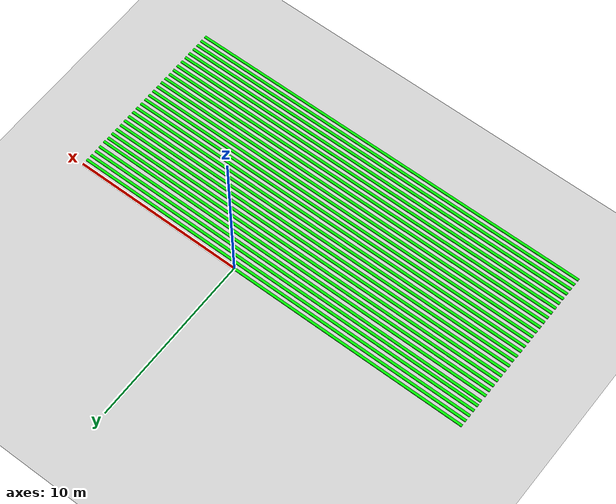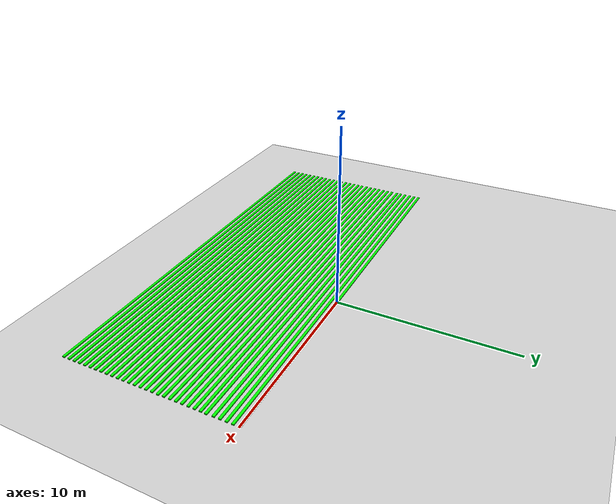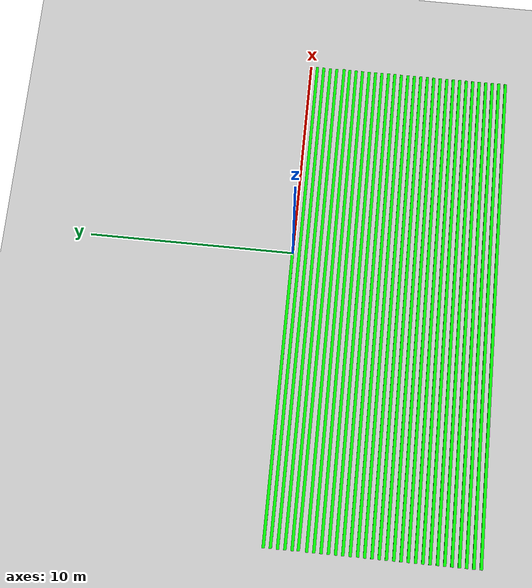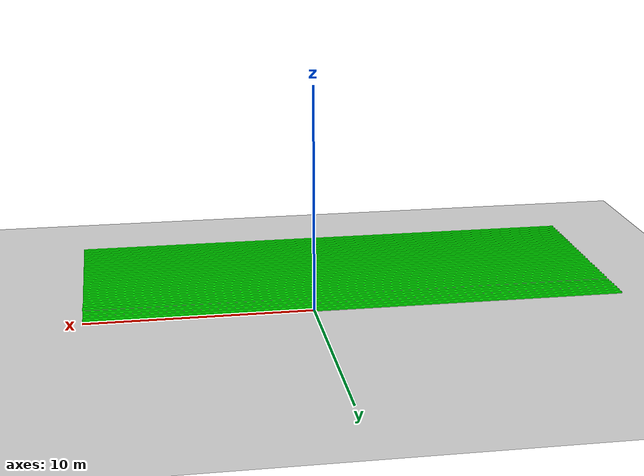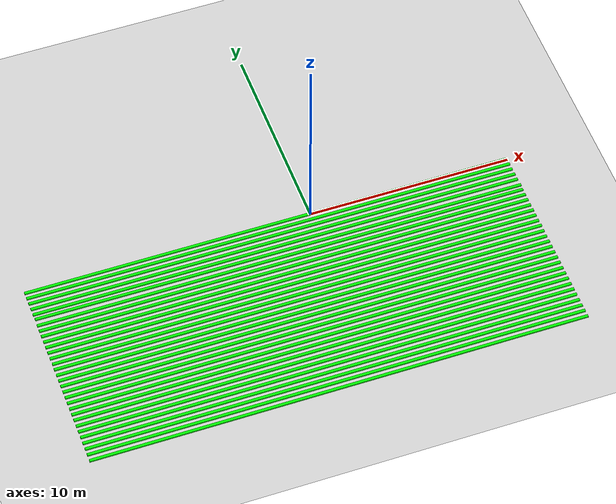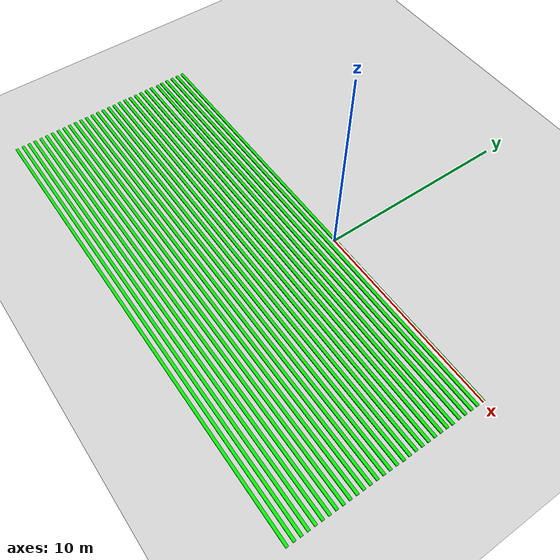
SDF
<sdf version="1.7">
 <world name="default">
  <light name="sun" type="directional">
   <pose>0 0 10 0 -0 0</pose>
   <diffuse>0.8 0.8 0.8 1</diffuse>
   <specular>0.2 0.2 0.2 1</specular>
   <attenuation>
    <range>1000</range>
    <constant>0.9</constant>
    <linear>0.01</linear>
    <quadratic>0.001</quadratic>
   </attenuation>
   <direction>-0.5 0.1 -0.9</direction>
   <spot><inner_angle>0</inner_angle><outer_angle>0</outer_angle><falloff>0</falloff></spot>
  </light>
  <model name="ground_plane">
   <static>1</static>
   <link name="link">
    <collision name="collision">
     <geometry><plane><normal>0 0 1</normal><size>100 100</size></plane></geometry>
     <surface>
      <contact><collide_bitmask>65535</collide_bitmask></contact>
      <friction><ode><mu>100</mu><mu2>50</mu2></ode></friction>
     </surface>
    </collision>
    <visual name="visual">
     <cast_shadows>0</cast_shadows>
     <geometry><plane><normal>0 0 1</normal><size>100 100</size></plane></geometry>
     <material>
      <script><uri>file://media/materials/scripts/gazebo.material</uri><name>Gazebo/Grey</name></script>
     </material>
    </visual>
   </link>
  </model>
  <gravity>0 0 -9.8</gravity>
  <magnetic_field>6e-06 2.3e-05 -4.2e-05</magnetic_field>
  <atmosphere type="adiabatic"/>
  <physics type="ode">
   <max_step_size>0.001</max_step_size>
   <real_time_factor>1</real_time_factor>
   <real_time_update_rate>1000</real_time_update_rate>
  </physics>
  <scene><ambient>0.4 0.4 0.4 1</ambient><background>0.7 0.7 0.7 1</background><shadows>1</shadows></scene>
  <spherical_coordinates>
   <surface_model>EARTH_WGS84</surface_model>
   <latitude_deg>0</latitude_deg>
   <longitude_deg>0</longitude_deg>
   <elevation>0</elevation>
   <heading_deg>0</heading_deg>
  </spherical_coordinates>
  <model name="one_crop_row">
   <link name="link_0">
    <inertial>
     <mass>9.98</mass>
     <inertia>
      <ixx>0.166667</ixx>
      <ixy>0</ixy>
      <ixz>0</ixz>
      <iyy>0.166667</iyy>
      <iyz>0</iyz>
      <izz>0.166667</izz>
     </inertia>
    </inertial>
    <visual name="visual">
     <geometry><mesh><uri>/home/devesh/one_crop_row.stl</uri><scale>1 1 1</scale></mesh></geometry>
     <material>
      <lighting>1</lighting>
      <script><uri>file://media/materials/scripts/gazebo.material</uri><name>Gazebo/Grey</name></script>
      <shader type="pixel"><normal_map>__default__</normal_map></shader>
      <ambient>0 1 0 0</ambient>
      <diffuse>0 1 0 0</diffuse>
      <specular>0 1 0 0</specular>
      <emissive>0 0 0 1</emissive>
     </material>
    </visual>
    <collision name="collision">
     <geometry><mesh><uri>/home/devesh/one_crop_row.stl</uri><scale>1 1 1</scale></mesh></geometry>
     <surface>
      <friction>
       <ode><mu>1</mu><mu2>1</mu2><fdir1>0 0 0</fdir1><slip1>0</slip1><slip2>0</slip2></ode>
       <torsional>
        <coefficient>1</coefficient>
        <patch_radius>0</patch_radius>
        <surface_radius>0</surface_radius>
        <use_patch_radius>1</use_patch_radius>
        <ode><slip>0</slip></ode>
       </torsional>
      </friction>
      <bounce><restitution_coefficient>0</restitution_coefficient><threshold>1e+06</threshold></bounce>
      <contact>
       <collide_without_contact>0</collide_without_contact>
       <collide_without_contact_bitmask>1</collide_without_contact_bitmask>
       <collide_bitmask>1</collide_bitmask>
       <ode>
        <soft_cfm>0</soft_cfm>
        <soft_erp>0.2</soft_erp>
        <kp>1e+13</kp>
        <kd>1</kd>
        <max_vel>0.01</max_vel>
        <min_depth>0</min_depth>
       </ode>
       <bullet>
        <split_impulse>1</split_impulse>
        <split_impulse_penetration_threshold>-0.01</split_impulse_penetration_threshold>
        <soft_cfm>0</soft_cfm>
        <soft_erp>0.2</soft_erp>
        <kp>1e+13</kp>
        <kd>1</kd>
       </bullet>
      </contact>
     </surface>
    </collision>
   </link>
   <static>0</static>
   <pose>-3.99983 0.000351 0.015873 -0.021911 -0 0.000378</pose>
  </model>
  <model name="one_crop_row_clone">
   <link name="link_0">
    <inertial>
     <mass>9.98</mass>
     <inertia>
      <ixx>0.166667</ixx>
      <ixy>0</ixy>
      <ixz>0</ixz>
      <iyy>0.166667</iyy>
      <iyz>0</iyz>
      <izz>0.166667</izz>
     </inertia>
    </inertial>
    <visual name="visual">
     <geometry><mesh><uri>/home/devesh/one_crop_row.stl</uri><scale>1 1 1</scale></mesh></geometry>
     <material>
      <lighting>1</lighting>
      <script><uri>file://media/materials/scripts/gazebo.material</uri><name>Gazebo/Grey</name></script>
      <shader type="pixel"><normal_map>__default__</normal_map></shader>
      <ambient>0 1 0 0</ambient>
      <diffuse>0 1 0 0</diffuse>
      <specular>0 1 0 0</specular>
      <emissive>0 0 0 1</emissive>
     </material>
    </visual>
    <collision name="collision">
     <geometry><mesh><uri>/home/devesh/one_crop_row.stl</uri><scale>1 1 1</scale></mesh></geometry>
     <surface>
      <friction>
       <ode><mu>1</mu><mu2>1</mu2><fdir1>0 0 0</fdir1><slip1>0</slip1><slip2>0</slip2></ode>
       <torsional>
        <coefficient>1</coefficient>
        <patch_radius>0</patch_radius>
        <surface_radius>0</surface_radius>
        <use_patch_radius>1</use_patch_radius>
        <ode><slip>0</slip></ode>
       </torsional>
      </friction>
      <bounce><restitution_coefficient>0</restitution_coefficient><threshold>1e+06</threshold></bounce>
      <contact>
       <collide_without_contact>0</collide_without_contact>
       <collide_without_contact_bitmask>1</collide_without_contact_bitmask>
       <collide_bitmask>1</collide_bitmask>
       <ode>
        <soft_cfm>0</soft_cfm>
        <soft_erp>0.2</soft_erp>
        <kp>1e+13</kp>
        <kd>1</kd>
        <max_vel>0.01</max_vel>
        <min_depth>0</min_depth>
       </ode>
       <bullet>
        <split_impulse>1</split_impulse>
        <split_impulse_penetration_threshold>-0.01</split_impulse_penetration_threshold>
        <soft_cfm>0</soft_cfm>
        <soft_erp>0.2</soft_erp>
        <kp>1e+13</kp>
        <kd>1</kd>
       </bullet>
      </contact>
     </surface>
    </collision>
   </link>
   <static>0</static>
   <pose>-3.99983 -0.999645 0.015872 -0.022099 -0 0.000191</pose>
  </model>
  <model name="one_crop_row_clone_0">
   <link name="link_0">
    <inertial>
     <mass>9.98</mass>
     <inertia>
      <ixx>0.166667</ixx>
      <ixy>0</ixy>
      <ixz>0</ixz>
      <iyy>0.166667</iyy>
      <iyz>0</iyz>
      <izz>0.166667</izz>
     </inertia>
    </inertial>
    <visual name="visual">
     <geometry><mesh><uri>/home/devesh/one_crop_row.stl</uri><scale>1 1 1</scale></mesh></geometry>
     <material>
      <lighting>1</lighting>
      <script><uri>file://media/materials/scripts/gazebo.material</uri><name>Gazebo/Grey</name></script>
      <shader type="pixel"><normal_map>__default__</normal_map></shader>
      <ambient>0 1 0 0</ambient>
      <diffuse>0 1 0 0</diffuse>
      <specular>0 1 0 0</specular>
      <emissive>0 0 0 1</emissive>
     </material>
    </visual>
    <collision name="collision">
     <geometry><mesh><uri>/home/devesh/one_crop_row.stl</uri><scale>1 1 1</scale></mesh></geometry>
     <surface>
      <friction>
       <ode><mu>1</mu><mu2>1</mu2><fdir1>0 0 0</fdir1><slip1>0</slip1><slip2>0</slip2></ode>
       <torsional>
        <coefficient>1</coefficient>
        <patch_radius>0</patch_radius>
        <surface_radius>0</surface_radius>
        <use_patch_radius>1</use_patch_radius>
        <ode><slip>0</slip></ode>
       </torsional>
      </friction>
      <bounce><restitution_coefficient>0</restitution_coefficient><threshold>1e+06</threshold></bounce>
      <contact>
       <collide_without_contact>0</collide_without_contact>
       <collide_without_contact_bitmask>1</collide_without_contact_bitmask>
       <collide_bitmask>1</collide_bitmask>
       <ode>
        <soft_cfm>0</soft_cfm>
        <soft_erp>0.2</soft_erp>
        <kp>1e+13</kp>
        <kd>1</kd>
        <max_vel>0.01</max_vel>
        <min_depth>0</min_depth>
       </ode>
       <bullet>
        <split_impulse>1</split_impulse>
        <split_impulse_penetration_threshold>-0.01</split_impulse_penetration_threshold>
        <soft_cfm>0</soft_cfm>
        <soft_erp>0.2</soft_erp>
        <kp>1e+13</kp>
        <kd>1</kd>
       </bullet>
      </contact>
     </surface>
    </collision>
   </link>
   <static>0</static>
   <pose>-3.99983 -0.329646 0.015865 -0.022038 3e-06 0.000193</pose>
  </model>
  <model name="one_crop_row_clone_1">
   <link name="link_0">
    <inertial>
     <mass>9.98</mass>
     <inertia>
      <ixx>0.166667</ixx>
      <ixy>0</ixy>
      <ixz>0</ixz>
      <iyy>0.166667</iyy>
      <iyz>0</iyz>
      <izz>0.166667</izz>
     </inertia>
    </inertial>
    <visual name="visual">
     <geometry><mesh><uri>/home/devesh/one_crop_row.stl</uri><scale>1 1 1</scale></mesh></geometry>
     <material>
      <lighting>1</lighting>
      <script><uri>file://media/materials/scripts/gazebo.material</uri><name>Gazebo/Grey</name></script>
      <shader type="pixel"><normal_map>__default__</normal_map></shader>
      <ambient>0 1 0 0</ambient>
      <diffuse>0 1 0 0</diffuse>
      <specular>0 1 0 0</specular>
      <emissive>0 0 0 1</emissive>
     </material>
    </visual>
    <collision name="collision">
     <geometry><mesh><uri>/home/devesh/one_crop_row.stl</uri><scale>1 1 1</scale></mesh></geometry>
     <surface>
      <friction>
       <ode><mu>1</mu><mu2>1</mu2><fdir1>0 0 0</fdir1><slip1>0</slip1><slip2>0</slip2></ode>
       <torsional>
        <coefficient>1</coefficient>
        <patch_radius>0</patch_radius>
        <surface_radius>0</surface_radius>
        <use_patch_radius>1</use_patch_radius>
        <ode><slip>0</slip></ode>
       </torsional>
      </friction>
      <bounce><restitution_coefficient>0</restitution_coefficient><threshold>1e+06</threshold></bounce>
      <contact>
       <collide_without_contact>0</collide_without_contact>
       <collide_without_contact_bitmask>1</collide_without_contact_bitmask>
       <collide_bitmask>1</collide_bitmask>
       <ode>
        <soft_cfm>0</soft_cfm>
        <soft_erp>0.2</soft_erp>
        <kp>1e+13</kp>
        <kd>1</kd>
        <max_vel>0.01</max_vel>
        <min_depth>0</min_depth>
       </ode>
       <bullet>
        <split_impulse>1</split_impulse>
        <split_impulse_penetration_threshold>-0.01</split_impulse_penetration_threshold>
        <soft_cfm>0</soft_cfm>
        <soft_erp>0.2</soft_erp>
        <kp>1e+13</kp>
        <kd>1</kd>
       </bullet>
      </contact>
     </surface>
    </collision>
   </link>
   <static>0</static>
   <pose>-3.99982 -0.659646 0.01587 -0.02203 1e-06 0.000192</pose>
  </model>
  <model name="one_crop_row_clone_2">
   <link name="link_0">
    <inertial>
     <mass>9.98</mass>
     <inertia>
      <ixx>0.166667</ixx>
      <ixy>0</ixy>
      <ixz>0</ixz>
      <iyy>0.166667</iyy>
      <iyz>0</iyz>
      <izz>0.166667</izz>
     </inertia>
    </inertial>
    <visual name="visual">
     <geometry><mesh><uri>/home/devesh/one_crop_row.stl</uri><scale>1 1 1</scale></mesh></geometry>
     <material>
      <lighting>1</lighting>
      <script><uri>file://media/materials/scripts/gazebo.material</uri><name>Gazebo/Grey</name></script>
      <shader type="pixel"><normal_map>__default__</normal_map></shader>
      <ambient>0 1 0 0</ambient>
      <diffuse>0 1 0 0</diffuse>
      <specular>0 1 0 0</specular>
      <emissive>0 0 0 1</emissive>
     </material>
    </visual>
    <collision name="collision">
     <geometry><mesh><uri>/home/devesh/one_crop_row.stl</uri><scale>1 1 1</scale></mesh></geometry>
     <surface>
      <friction>
       <ode><mu>1</mu><mu2>1</mu2><fdir1>0 0 0</fdir1><slip1>0</slip1><slip2>0</slip2></ode>
       <torsional>
        <coefficient>1</coefficient>
        <patch_radius>0</patch_radius>
        <surface_radius>0</surface_radius>
        <use_patch_radius>1</use_patch_radius>
        <ode><slip>0</slip></ode>
       </torsional>
      </friction>
      <bounce><restitution_coefficient>0</restitution_coefficient><threshold>1e+06</threshold></bounce>
      <contact>
       <collide_without_contact>0</collide_without_contact>
       <collide_without_contact_bitmask>1</collide_without_contact_bitmask>
       <collide_bitmask>1</collide_bitmask>
       <ode>
        <soft_cfm>0</soft_cfm>
        <soft_erp>0.2</soft_erp>
        <kp>1e+13</kp>
        <kd>1</kd>
        <max_vel>0.01</max_vel>
        <min_depth>0</min_depth>
       </ode>
       <bullet>
        <split_impulse>1</split_impulse>
        <split_impulse_penetration_threshold>-0.01</split_impulse_penetration_threshold>
        <soft_cfm>0</soft_cfm>
        <soft_erp>0.2</soft_erp>
        <kp>1e+13</kp>
        <kd>1</kd>
       </bullet>
      </contact>
     </surface>
    </collision>
   </link>
   <static>0</static>
   <pose>-3.99983 -1.99967 0.015867 -0.02188 2e-06 0.000137</pose>
  </model>
  <model name="one_crop_row_clone_3">
   <link name="link_0">
    <inertial>
     <mass>9.98</mass>
     <inertia>
      <ixx>0.166667</ixx>
      <ixy>0</ixy>
      <ixz>0</ixz>
      <iyy>0.166667</iyy>
      <iyz>0</iyz>
      <izz>0.166667</izz>
     </inertia>
    </inertial>
    <visual name="visual">
     <geometry><mesh><uri>/home/devesh/one_crop_row.stl</uri><scale>1 1 1</scale></mesh></geometry>
     <material>
      <lighting>1</lighting>
      <script><uri>file://media/materials/scripts/gazebo.material</uri><name>Gazebo/Grey</name></script>
      <shader type="pixel"><normal_map>__default__</normal_map></shader>
      <ambient>0 1 0 0</ambient>
      <diffuse>0 1 0 0</diffuse>
      <specular>0 1 0 0</specular>
      <emissive>0 0 0 1</emissive>
     </material>
    </visual>
    <collision name="collision">
     <geometry><mesh><uri>/home/devesh/one_crop_row.stl</uri><scale>1 1 1</scale></mesh></geometry>
     <surface>
      <friction>
       <ode><mu>1</mu><mu2>1</mu2><fdir1>0 0 0</fdir1><slip1>0</slip1><slip2>0</slip2></ode>
       <torsional>
        <coefficient>1</coefficient>
        <patch_radius>0</patch_radius>
        <surface_radius>0</surface_radius>
        <use_patch_radius>1</use_patch_radius>
        <ode><slip>0</slip></ode>
       </torsional>
      </friction>
      <bounce><restitution_coefficient>0</restitution_coefficient><threshold>1e+06</threshold></bounce>
      <contact>
       <collide_without_contact>0</collide_without_contact>
       <collide_without_contact_bitmask>1</collide_without_contact_bitmask>
       <collide_bitmask>1</collide_bitmask>
       <ode>
        <soft_cfm>0</soft_cfm>
        <soft_erp>0.2</soft_erp>
        <kp>1e+13</kp>
        <kd>1</kd>
        <max_vel>0.01</max_vel>
        <min_depth>0</min_depth>
       </ode>
       <bullet>
        <split_impulse>1</split_impulse>
        <split_impulse_penetration_threshold>-0.01</split_impulse_penetration_threshold>
        <soft_cfm>0</soft_cfm>
        <soft_erp>0.2</soft_erp>
        <kp>1e+13</kp>
        <kd>1</kd>
       </bullet>
      </contact>
     </surface>
    </collision>
   </link>
   <static>0</static>
   <pose>-3.99982 -1.32965 0.015867 -0.022063 8e-06 0.000171</pose>
  </model>
  <model name="one_crop_row_clone_4">
   <link name="link_0">
    <inertial>
     <mass>9.98</mass>
     <inertia>
      <ixx>0.166667</ixx>
      <ixy>0</ixy>
      <ixz>0</ixz>
      <iyy>0.166667</iyy>
      <iyz>0</iyz>
      <izz>0.166667</izz>
     </inertia>
    </inertial>
    <visual name="visual">
     <geometry><mesh><uri>/home/devesh/one_crop_row.stl</uri><scale>1 1 1</scale></mesh></geometry>
     <material>
      <lighting>1</lighting>
      <script><uri>file://media/materials/scripts/gazebo.material</uri><name>Gazebo/Grey</name></script>
      <shader type="pixel"><normal_map>__default__</normal_map></shader>
      <ambient>0 1 0 0</ambient>
      <diffuse>0 1 0 0</diffuse>
      <specular>0 1 0 0</specular>
      <emissive>0 0 0 1</emissive>
     </material>
    </visual>
    <collision name="collision">
     <geometry><mesh><uri>/home/devesh/one_crop_row.stl</uri><scale>1 1 1</scale></mesh></geometry>
     <surface>
      <friction>
       <ode><mu>1</mu><mu2>1</mu2><fdir1>0 0 0</fdir1><slip1>0</slip1><slip2>0</slip2></ode>
       <torsional>
        <coefficient>1</coefficient>
        <patch_radius>0</patch_radius>
        <surface_radius>0</surface_radius>
        <use_patch_radius>1</use_patch_radius>
        <ode><slip>0</slip></ode>
       </torsional>
      </friction>
      <bounce><restitution_coefficient>0</restitution_coefficient><threshold>1e+06</threshold></bounce>
      <contact>
       <collide_without_contact>0</collide_without_contact>
       <collide_without_contact_bitmask>1</collide_without_contact_bitmask>
       <collide_bitmask>1</collide_bitmask>
       <ode>
        <soft_cfm>0</soft_cfm>
        <soft_erp>0.2</soft_erp>
        <kp>1e+13</kp>
        <kd>1</kd>
        <max_vel>0.01</max_vel>
        <min_depth>0</min_depth>
       </ode>
       <bullet>
        <split_impulse>1</split_impulse>
        <split_impulse_penetration_threshold>-0.01</split_impulse_penetration_threshold>
        <soft_cfm>0</soft_cfm>
        <soft_erp>0.2</soft_erp>
        <kp>1e+13</kp>
        <kd>1</kd>
       </bullet>
      </contact>
     </surface>
    </collision>
   </link>
   <static>0</static>
   <pose>-3.97938 -1.65398 0.015864 -0.022063 3e-06 -0.003681</pose>
  </model>
  <model name="one_crop_row_clone_5">
   <link name="link_0">
    <inertial>
     <mass>9.98</mass>
     <inertia>
      <ixx>0.166667</ixx>
      <ixy>0</ixy>
      <ixz>0</ixz>
      <iyy>0.166667</iyy>
      <iyz>0</iyz>
      <izz>0.166667</izz>
     </inertia>
    </inertial>
    <visual name="visual">
     <geometry><mesh><uri>/home/devesh/one_crop_row.stl</uri><scale>1 1 1</scale></mesh></geometry>
     <material>
      <lighting>1</lighting>
      <script><uri>file://media/materials/scripts/gazebo.material</uri><name>Gazebo/Grey</name></script>
      <shader type="pixel"><normal_map>__default__</normal_map></shader>
      <ambient>0 1 0 0</ambient>
      <diffuse>0 1 0 0</diffuse>
      <specular>0 1 0 0</specular>
      <emissive>0 0 0 1</emissive>
     </material>
    </visual>
    <collision name="collision">
     <geometry><mesh><uri>/home/devesh/one_crop_row.stl</uri><scale>1 1 1</scale></mesh></geometry>
     <surface>
      <friction>
       <ode><mu>1</mu><mu2>1</mu2><fdir1>0 0 0</fdir1><slip1>0</slip1><slip2>0</slip2></ode>
       <torsional>
        <coefficient>1</coefficient>
        <patch_radius>0</patch_radius>
        <surface_radius>0</surface_radius>
        <use_patch_radius>1</use_patch_radius>
        <ode><slip>0</slip></ode>
       </torsional>
      </friction>
      <bounce><restitution_coefficient>0</restitution_coefficient><threshold>1e+06</threshold></bounce>
      <contact>
       <collide_without_contact>0</collide_without_contact>
       <collide_without_contact_bitmask>1</collide_without_contact_bitmask>
       <collide_bitmask>1</collide_bitmask>
       <ode>
        <soft_cfm>0</soft_cfm>
        <soft_erp>0.2</soft_erp>
        <kp>1e+13</kp>
        <kd>1</kd>
        <max_vel>0.01</max_vel>
        <min_depth>0</min_depth>
       </ode>
       <bullet>
        <split_impulse>1</split_impulse>
        <split_impulse_penetration_threshold>-0.01</split_impulse_penetration_threshold>
        <soft_cfm>0</soft_cfm>
        <soft_erp>0.2</soft_erp>
        <kp>1e+13</kp>
        <kd>1</kd>
       </bullet>
      </contact>
     </surface>
    </collision>
   </link>
   <static>0</static>
   <pose>-3.99981 -2.99965 0.015872 -0.022099 -0 0.000179</pose>
  </model>
  <model name="one_crop_row_clone_6">
   <link name="link_0">
    <inertial>
     <mass>9.98</mass>
     <inertia>
      <ixx>0.166667</ixx>
      <ixy>0</ixy>
      <ixz>0</ixz>
      <iyy>0.166667</iyy>
      <iyz>0</iyz>
      <izz>0.166667</izz>
     </inertia>
    </inertial>
    <visual name="visual">
     <geometry><mesh><uri>/home/devesh/one_crop_row.stl</uri><scale>1 1 1</scale></mesh></geometry>
     <material>
      <lighting>1</lighting>
      <script><uri>file://media/materials/scripts/gazebo.material</uri><name>Gazebo/Grey</name></script>
      <shader type="pixel"><normal_map>__default__</normal_map></shader>
      <ambient>0 1 0 0</ambient>
      <diffuse>0 1 0 0</diffuse>
      <specular>0 1 0 0</specular>
      <emissive>0 0 0 1</emissive>
     </material>
    </visual>
    <collision name="collision">
     <geometry><mesh><uri>/home/devesh/one_crop_row.stl</uri><scale>1 1 1</scale></mesh></geometry>
     <surface>
      <friction>
       <ode><mu>1</mu><mu2>1</mu2><fdir1>0 0 0</fdir1><slip1>0</slip1><slip2>0</slip2></ode>
       <torsional>
        <coefficient>1</coefficient>
        <patch_radius>0</patch_radius>
        <surface_radius>0</surface_radius>
        <use_patch_radius>1</use_patch_radius>
        <ode><slip>0</slip></ode>
       </torsional>
      </friction>
      <bounce><restitution_coefficient>0</restitution_coefficient><threshold>1e+06</threshold></bounce>
      <contact>
       <collide_without_contact>0</collide_without_contact>
       <collide_without_contact_bitmask>1</collide_without_contact_bitmask>
       <collide_bitmask>1</collide_bitmask>
       <ode>
        <soft_cfm>0</soft_cfm>
        <soft_erp>0.2</soft_erp>
        <kp>1e+13</kp>
        <kd>1</kd>
        <max_vel>0.01</max_vel>
        <min_depth>0</min_depth>
       </ode>
       <bullet>
        <split_impulse>1</split_impulse>
        <split_impulse_penetration_threshold>-0.01</split_impulse_penetration_threshold>
        <soft_cfm>0</soft_cfm>
        <soft_erp>0.2</soft_erp>
        <kp>1e+13</kp>
        <kd>1</kd>
       </bullet>
      </contact>
     </surface>
    </collision>
   </link>
   <static>0</static>
   <pose>-3.99983 -2.32965 0.015872 -0.022091 -0 0.000194</pose>
  </model>
  <model name="one_crop_row_clone_7">
   <link name="link_0">
    <inertial>
     <mass>9.98</mass>
     <inertia>
      <ixx>0.166667</ixx>
      <ixy>0</ixy>
      <ixz>0</ixz>
      <iyy>0.166667</iyy>
      <iyz>0</iyz>
      <izz>0.166667</izz>
     </inertia>
    </inertial>
    <visual name="visual">
     <geometry><mesh><uri>/home/devesh/one_crop_row.stl</uri><scale>1 1 1</scale></mesh></geometry>
     <material>
      <lighting>1</lighting>
      <script><uri>file://media/materials/scripts/gazebo.material</uri><name>Gazebo/Grey</name></script>
      <shader type="pixel"><normal_map>__default__</normal_map></shader>
      <ambient>0 1 0 0</ambient>
      <diffuse>0 1 0 0</diffuse>
      <specular>0 1 0 0</specular>
      <emissive>0 0 0 1</emissive>
     </material>
    </visual>
    <collision name="collision">
     <geometry><mesh><uri>/home/devesh/one_crop_row.stl</uri><scale>1 1 1</scale></mesh></geometry>
     <surface>
      <friction>
       <ode><mu>1</mu><mu2>1</mu2><fdir1>0 0 0</fdir1><slip1>0</slip1><slip2>0</slip2></ode>
       <torsional>
        <coefficient>1</coefficient>
        <patch_radius>0</patch_radius>
        <surface_radius>0</surface_radius>
        <use_patch_radius>1</use_patch_radius>
        <ode><slip>0</slip></ode>
       </torsional>
      </friction>
      <bounce><restitution_coefficient>0</restitution_coefficient><threshold>1e+06</threshold></bounce>
      <contact>
       <collide_without_contact>0</collide_without_contact>
       <collide_without_contact_bitmask>1</collide_without_contact_bitmask>
       <collide_bitmask>1</collide_bitmask>
       <ode>
        <soft_cfm>0</soft_cfm>
        <soft_erp>0.2</soft_erp>
        <kp>1e+13</kp>
        <kd>1</kd>
        <max_vel>0.01</max_vel>
        <min_depth>0</min_depth>
       </ode>
       <bullet>
        <split_impulse>1</split_impulse>
        <split_impulse_penetration_threshold>-0.01</split_impulse_penetration_threshold>
        <soft_cfm>0</soft_cfm>
        <soft_erp>0.2</soft_erp>
        <kp>1e+13</kp>
        <kd>1</kd>
       </bullet>
      </contact>
     </surface>
    </collision>
   </link>
   <static>0</static>
   <pose>-3.99985 -2.65965 0.015872 -0.022066 0 0.000194</pose>
  </model>
  <model name="one_crop_row_clone_8">
   <link name="link_0">
    <inertial>
     <mass>9.98</mass>
     <inertia>
      <ixx>0.166667</ixx>
      <ixy>0</ixy>
      <ixz>0</ixz>
      <iyy>0.166667</iyy>
      <iyz>0</iyz>
      <izz>0.166667</izz>
     </inertia>
    </inertial>
    <visual name="visual">
     <geometry><mesh><uri>/home/devesh/one_crop_row.stl</uri><scale>1 1 1</scale></mesh></geometry>
     <material>
      <lighting>1</lighting>
      <script><uri>file://media/materials/scripts/gazebo.material</uri><name>Gazebo/Grey</name></script>
      <shader type="pixel"><normal_map>__default__</normal_map></shader>
      <ambient>0 1 0 0</ambient>
      <diffuse>0 1 0 0</diffuse>
      <specular>0 1 0 0</specular>
      <emissive>0 0 0 1</emissive>
     </material>
    </visual>
    <collision name="collision">
     <geometry><mesh><uri>/home/devesh/one_crop_row.stl</uri><scale>1 1 1</scale></mesh></geometry>
     <surface>
      <friction>
       <ode><mu>1</mu><mu2>1</mu2><fdir1>0 0 0</fdir1><slip1>0</slip1><slip2>0</slip2></ode>
       <torsional>
        <coefficient>1</coefficient>
        <patch_radius>0</patch_radius>
        <surface_radius>0</surface_radius>
        <use_patch_radius>1</use_patch_radius>
        <ode><slip>0</slip></ode>
       </torsional>
      </friction>
      <bounce><restitution_coefficient>0</restitution_coefficient><threshold>1e+06</threshold></bounce>
      <contact>
       <collide_without_contact>0</collide_without_contact>
       <collide_without_contact_bitmask>1</collide_without_contact_bitmask>
       <collide_bitmask>1</collide_bitmask>
       <ode>
        <soft_cfm>0</soft_cfm>
        <soft_erp>0.2</soft_erp>
        <kp>1e+13</kp>
        <kd>1</kd>
        <max_vel>0.01</max_vel>
        <min_depth>0</min_depth>
       </ode>
       <bullet>
        <split_impulse>1</split_impulse>
        <split_impulse_penetration_threshold>-0.01</split_impulse_penetration_threshold>
        <soft_cfm>0</soft_cfm>
        <soft_erp>0.2</soft_erp>
        <kp>1e+13</kp>
        <kd>1</kd>
       </bullet>
      </contact>
     </surface>
    </collision>
   </link>
   <static>0</static>
   <pose>-3.99984 -3.99965 0.015866 -0.021961 2e-06 0.000196</pose>
  </model>
  <model name="one_crop_row_clone_9">
   <link name="link_0">
    <inertial>
     <mass>9.98</mass>
     <inertia>
      <ixx>0.166667</ixx>
      <ixy>0</ixy>
      <ixz>0</ixz>
      <iyy>0.166667</iyy>
      <iyz>0</iyz>
      <izz>0.166667</izz>
     </inertia>
    </inertial>
    <visual name="visual">
     <geometry><mesh><uri>/home/devesh/one_crop_row.stl</uri><scale>1 1 1</scale></mesh></geometry>
     <material>
      <lighting>1</lighting>
      <script><uri>file://media/materials/scripts/gazebo.material</uri><name>Gazebo/Grey</name></script>
      <shader type="pixel"><normal_map>__default__</normal_map></shader>
      <ambient>0 1 0 0</ambient>
      <diffuse>0 1 0 0</diffuse>
      <specular>0 1 0 0</specular>
      <emissive>0 0 0 1</emissive>
     </material>
    </visual>
    <collision name="collision">
     <geometry><mesh><uri>/home/devesh/one_crop_row.stl</uri><scale>1 1 1</scale></mesh></geometry>
     <surface>
      <friction>
       <ode><mu>1</mu><mu2>1</mu2><fdir1>0 0 0</fdir1><slip1>0</slip1><slip2>0</slip2></ode>
       <torsional>
        <coefficient>1</coefficient>
        <patch_radius>0</patch_radius>
        <surface_radius>0</surface_radius>
        <use_patch_radius>1</use_patch_radius>
        <ode><slip>0</slip></ode>
       </torsional>
      </friction>
      <bounce><restitution_coefficient>0</restitution_coefficient><threshold>1e+06</threshold></bounce>
      <contact>
       <collide_without_contact>0</collide_without_contact>
       <collide_without_contact_bitmask>1</collide_without_contact_bitmask>
       <collide_bitmask>1</collide_bitmask>
       <ode>
        <soft_cfm>0</soft_cfm>
        <soft_erp>0.2</soft_erp>
        <kp>1e+13</kp>
        <kd>1</kd>
        <max_vel>0.01</max_vel>
        <min_depth>0</min_depth>
       </ode>
       <bullet>
        <split_impulse>1</split_impulse>
        <split_impulse_penetration_threshold>-0.01</split_impulse_penetration_threshold>
        <soft_cfm>0</soft_cfm>
        <soft_erp>0.2</soft_erp>
        <kp>1e+13</kp>
        <kd>1</kd>
       </bullet>
      </contact>
     </surface>
    </collision>
   </link>
   <static>0</static>
   <pose>-3.99983 -3.32965 0.015872 -0.022056 -0 0.000194</pose>
  </model>
  <model name="one_crop_row_clone_10">
   <link name="link_0">
    <inertial>
     <mass>9.98</mass>
     <inertia>
      <ixx>0.166667</ixx>
      <ixy>0</ixy>
      <ixz>0</ixz>
      <iyy>0.166667</iyy>
      <iyz>0</iyz>
      <izz>0.166667</izz>
     </inertia>
    </inertial>
    <visual name="visual">
     <geometry><mesh><uri>/home/devesh/one_crop_row.stl</uri><scale>1 1 1</scale></mesh></geometry>
     <material>
      <lighting>1</lighting>
      <script><uri>file://media/materials/scripts/gazebo.material</uri><name>Gazebo/Grey</name></script>
      <shader type="pixel"><normal_map>__default__</normal_map></shader>
      <ambient>0 1 0 0</ambient>
      <diffuse>0 1 0 0</diffuse>
      <specular>0 1 0 0</specular>
      <emissive>0 0 0 1</emissive>
     </material>
    </visual>
    <collision name="collision">
     <geometry><mesh><uri>/home/devesh/one_crop_row.stl</uri><scale>1 1 1</scale></mesh></geometry>
     <surface>
      <friction>
       <ode><mu>1</mu><mu2>1</mu2><fdir1>0 0 0</fdir1><slip1>0</slip1><slip2>0</slip2></ode>
       <torsional>
        <coefficient>1</coefficient>
        <patch_radius>0</patch_radius>
        <surface_radius>0</surface_radius>
        <use_patch_radius>1</use_patch_radius>
        <ode><slip>0</slip></ode>
       </torsional>
      </friction>
      <bounce><restitution_coefficient>0</restitution_coefficient><threshold>1e+06</threshold></bounce>
      <contact>
       <collide_without_contact>0</collide_without_contact>
       <collide_without_contact_bitmask>1</collide_without_contact_bitmask>
       <collide_bitmask>1</collide_bitmask>
       <ode>
        <soft_cfm>0</soft_cfm>
        <soft_erp>0.2</soft_erp>
        <kp>1e+13</kp>
        <kd>1</kd>
        <max_vel>0.01</max_vel>
        <min_depth>0</min_depth>
       </ode>
       <bullet>
        <split_impulse>1</split_impulse>
        <split_impulse_penetration_threshold>-0.01</split_impulse_penetration_threshold>
        <soft_cfm>0</soft_cfm>
        <soft_erp>0.2</soft_erp>
        <kp>1e+13</kp>
        <kd>1</kd>
       </bullet>
      </contact>
     </surface>
    </collision>
   </link>
   <static>0</static>
   <pose>-3.99983 -3.65965 0.015872 -0.022099 -0 0.000194</pose>
  </model>
  <model name="one_crop_row_clone_11">
   <link name="link_0">
    <inertial>
     <mass>9.98</mass>
     <inertia>
      <ixx>0.166667</ixx>
      <ixy>0</ixy>
      <ixz>0</ixz>
      <iyy>0.166667</iyy>
      <iyz>0</iyz>
      <izz>0.166667</izz>
     </inertia>
    </inertial>
    <visual name="visual">
     <geometry><mesh><uri>/home/devesh/one_crop_row.stl</uri><scale>1 1 1</scale></mesh></geometry>
     <material>
      <lighting>1</lighting>
      <script><uri>file://media/materials/scripts/gazebo.material</uri><name>Gazebo/Grey</name></script>
      <shader type="pixel"><normal_map>__default__</normal_map></shader>
      <ambient>0 1 0 0</ambient>
      <diffuse>0 1 0 0</diffuse>
      <specular>0 1 0 0</specular>
      <emissive>0 0 0 1</emissive>
     </material>
    </visual>
    <collision name="collision">
     <geometry><mesh><uri>/home/devesh/one_crop_row.stl</uri><scale>1 1 1</scale></mesh></geometry>
     <surface>
      <friction>
       <ode><mu>1</mu><mu2>1</mu2><fdir1>0 0 0</fdir1><slip1>0</slip1><slip2>0</slip2></ode>
       <torsional>
        <coefficient>1</coefficient>
        <patch_radius>0</patch_radius>
        <surface_radius>0</surface_radius>
        <use_patch_radius>1</use_patch_radius>
        <ode><slip>0</slip></ode>
       </torsional>
      </friction>
      <bounce><restitution_coefficient>0</restitution_coefficient><threshold>1e+06</threshold></bounce>
      <contact>
       <collide_without_contact>0</collide_without_contact>
       <collide_without_contact_bitmask>1</collide_without_contact_bitmask>
       <collide_bitmask>1</collide_bitmask>
       <ode>
        <soft_cfm>0</soft_cfm>
        <soft_erp>0.2</soft_erp>
        <kp>1e+13</kp>
        <kd>1</kd>
        <max_vel>0.01</max_vel>
        <min_depth>0</min_depth>
       </ode>
       <bullet>
        <split_impulse>1</split_impulse>
        <split_impulse_penetration_threshold>-0.01</split_impulse_penetration_threshold>
        <soft_cfm>0</soft_cfm>
        <soft_erp>0.2</soft_erp>
        <kp>1e+13</kp>
        <kd>1</kd>
       </bullet>
      </contact>
     </surface>
    </collision>
   </link>
   <static>0</static>
   <pose>-3.99982 -4.99965 0.015865 -0.022106 9e-06 0.000194</pose>
  </model>
  <model name="one_crop_row_clone_12">
   <link name="link_0">
    <inertial>
     <mass>9.98</mass>
     <inertia>
      <ixx>0.166667</ixx>
      <ixy>0</ixy>
      <ixz>0</ixz>
      <iyy>0.166667</iyy>
      <iyz>0</iyz>
      <izz>0.166667</izz>
     </inertia>
    </inertial>
    <visual name="visual">
     <geometry><mesh><uri>/home/devesh/one_crop_row.stl</uri><scale>1 1 1</scale></mesh></geometry>
     <material>
      <lighting>1</lighting>
      <script><uri>file://media/materials/scripts/gazebo.material</uri><name>Gazebo/Grey</name></script>
      <shader type="pixel"><normal_map>__default__</normal_map></shader>
      <ambient>0 1 0 0</ambient>
      <diffuse>0 1 0 0</diffuse>
      <specular>0 1 0 0</specular>
      <emissive>0 0 0 1</emissive>
     </material>
    </visual>
    <collision name="collision">
     <geometry><mesh><uri>/home/devesh/one_crop_row.stl</uri><scale>1 1 1</scale></mesh></geometry>
     <surface>
      <friction>
       <ode><mu>1</mu><mu2>1</mu2><fdir1>0 0 0</fdir1><slip1>0</slip1><slip2>0</slip2></ode>
       <torsional>
        <coefficient>1</coefficient>
        <patch_radius>0</patch_radius>
        <surface_radius>0</surface_radius>
        <use_patch_radius>1</use_patch_radius>
        <ode><slip>0</slip></ode>
       </torsional>
      </friction>
      <bounce><restitution_coefficient>0</restitution_coefficient><threshold>1e+06</threshold></bounce>
      <contact>
       <collide_without_contact>0</collide_without_contact>
       <collide_without_contact_bitmask>1</collide_without_contact_bitmask>
       <collide_bitmask>1</collide_bitmask>
       <ode>
        <soft_cfm>0</soft_cfm>
        <soft_erp>0.2</soft_erp>
        <kp>1e+13</kp>
        <kd>1</kd>
        <max_vel>0.01</max_vel>
        <min_depth>0</min_depth>
       </ode>
       <bullet>
        <split_impulse>1</split_impulse>
        <split_impulse_penetration_threshold>-0.01</split_impulse_penetration_threshold>
        <soft_cfm>0</soft_cfm>
        <soft_erp>0.2</soft_erp>
        <kp>1e+13</kp>
        <kd>1</kd>
       </bullet>
      </contact>
     </surface>
    </collision>
   </link>
   <static>0</static>
   <pose>-3.98527 -4.33129 0.015872 -0.022031 0 0.00081</pose>
  </model>
  <model name="one_crop_row_clone_13">
   <link name="link_0">
    <inertial>
     <mass>9.98</mass>
     <inertia>
      <ixx>0.166667</ixx>
      <ixy>0</ixy>
      <ixz>0</ixz>
      <iyy>0.166667</iyy>
      <iyz>0</iyz>
      <izz>0.166667</izz>
     </inertia>
    </inertial>
    <visual name="visual">
     <geometry><mesh><uri>/home/devesh/one_crop_row.stl</uri><scale>1 1 1</scale></mesh></geometry>
     <material>
      <lighting>1</lighting>
      <script><uri>file://media/materials/scripts/gazebo.material</uri><name>Gazebo/Grey</name></script>
      <shader type="pixel"><normal_map>__default__</normal_map></shader>
      <ambient>0 1 0 0</ambient>
      <diffuse>0 1 0 0</diffuse>
      <specular>0 1 0 0</specular>
      <emissive>0 0 0 1</emissive>
     </material>
    </visual>
    <collision name="collision">
     <geometry><mesh><uri>/home/devesh/one_crop_row.stl</uri><scale>1 1 1</scale></mesh></geometry>
     <surface>
      <friction>
       <ode><mu>1</mu><mu2>1</mu2><fdir1>0 0 0</fdir1><slip1>0</slip1><slip2>0</slip2></ode>
       <torsional>
        <coefficient>1</coefficient>
        <patch_radius>0</patch_radius>
        <surface_radius>0</surface_radius>
        <use_patch_radius>1</use_patch_radius>
        <ode><slip>0</slip></ode>
       </torsional>
      </friction>
      <bounce><restitution_coefficient>0</restitution_coefficient><threshold>1e+06</threshold></bounce>
      <contact>
       <collide_without_contact>0</collide_without_contact>
       <collide_without_contact_bitmask>1</collide_without_contact_bitmask>
       <collide_bitmask>1</collide_bitmask>
       <ode>
        <soft_cfm>0</soft_cfm>
        <soft_erp>0.2</soft_erp>
        <kp>1e+13</kp>
        <kd>1</kd>
        <max_vel>0.01</max_vel>
        <min_depth>0</min_depth>
       </ode>
       <bullet>
        <split_impulse>1</split_impulse>
        <split_impulse_penetration_threshold>-0.01</split_impulse_penetration_threshold>
        <soft_cfm>0</soft_cfm>
        <soft_erp>0.2</soft_erp>
        <kp>1e+13</kp>
        <kd>1</kd>
       </bullet>
      </contact>
     </surface>
    </collision>
   </link>
   <static>0</static>
   <pose>-3.99983 -4.65971 0.015873 -0.021999 -0 0.000128</pose>
  </model>
  <model name="one_crop_row_clone_14">
   <link name="link_0">
    <inertial>
     <mass>9.98</mass>
     <inertia>
      <ixx>0.166667</ixx>
      <ixy>0</ixy>
      <ixz>0</ixz>
      <iyy>0.166667</iyy>
      <iyz>0</iyz>
      <izz>0.166667</izz>
     </inertia>
    </inertial>
    <visual name="visual">
     <geometry><mesh><uri>/home/devesh/one_crop_row.stl</uri><scale>1 1 1</scale></mesh></geometry>
     <material>
      <lighting>1</lighting>
      <script><uri>file://media/materials/scripts/gazebo.material</uri><name>Gazebo/Grey</name></script>
      <shader type="pixel"><normal_map>__default__</normal_map></shader>
      <ambient>0 1 0 0</ambient>
      <diffuse>0 1 0 0</diffuse>
      <specular>0 1 0 0</specular>
      <emissive>0 0 0 1</emissive>
     </material>
    </visual>
    <collision name="collision">
     <geometry><mesh><uri>/home/devesh/one_crop_row.stl</uri><scale>1 1 1</scale></mesh></geometry>
     <surface>
      <friction>
       <ode><mu>1</mu><mu2>1</mu2><fdir1>0 0 0</fdir1><slip1>0</slip1><slip2>0</slip2></ode>
       <torsional>
        <coefficient>1</coefficient>
        <patch_radius>0</patch_radius>
        <surface_radius>0</surface_radius>
        <use_patch_radius>1</use_patch_radius>
        <ode><slip>0</slip></ode>
       </torsional>
      </friction>
      <bounce><restitution_coefficient>0</restitution_coefficient><threshold>1e+06</threshold></bounce>
      <contact>
       <collide_without_contact>0</collide_without_contact>
       <collide_without_contact_bitmask>1</collide_without_contact_bitmask>
       <collide_bitmask>1</collide_bitmask>
       <ode>
        <soft_cfm>0</soft_cfm>
        <soft_erp>0.2</soft_erp>
        <kp>1e+13</kp>
        <kd>1</kd>
        <max_vel>0.01</max_vel>
        <min_depth>0</min_depth>
       </ode>
       <bullet>
        <split_impulse>1</split_impulse>
        <split_impulse_penetration_threshold>-0.01</split_impulse_penetration_threshold>
        <soft_cfm>0</soft_cfm>
        <soft_erp>0.2</soft_erp>
        <kp>1e+13</kp>
        <kd>1</kd>
       </bullet>
      </contact>
     </surface>
    </collision>
   </link>
   <static>0</static>
   <pose>-3.99981 -5.99965 0.01587 -0.022081 -3e-06 0.000191</pose>
  </model>
  <model name="one_crop_row_clone_15">
   <link name="link_0">
    <inertial>
     <mass>9.98</mass>
     <inertia>
      <ixx>0.166667</ixx>
      <ixy>0</ixy>
      <ixz>0</ixz>
      <iyy>0.166667</iyy>
      <iyz>0</iyz>
      <izz>0.166667</izz>
     </inertia>
    </inertial>
    <visual name="visual">
     <geometry><mesh><uri>/home/devesh/one_crop_row.stl</uri><scale>1 1 1</scale></mesh></geometry>
     <material>
      <lighting>1</lighting>
      <script><uri>file://media/materials/scripts/gazebo.material</uri><name>Gazebo/Grey</name></script>
      <shader type="pixel"><normal_map>__default__</normal_map></shader>
      <ambient>0 1 0 0</ambient>
      <diffuse>0 1 0 0</diffuse>
      <specular>0 1 0 0</specular>
      <emissive>0 0 0 1</emissive>
     </material>
    </visual>
    <collision name="collision">
     <geometry><mesh><uri>/home/devesh/one_crop_row.stl</uri><scale>1 1 1</scale></mesh></geometry>
     <surface>
      <friction>
       <ode><mu>1</mu><mu2>1</mu2><fdir1>0 0 0</fdir1><slip1>0</slip1><slip2>0</slip2></ode>
       <torsional>
        <coefficient>1</coefficient>
        <patch_radius>0</patch_radius>
        <surface_radius>0</surface_radius>
        <use_patch_radius>1</use_patch_radius>
        <ode><slip>0</slip></ode>
       </torsional>
      </friction>
      <bounce><restitution_coefficient>0</restitution_coefficient><threshold>1e+06</threshold></bounce>
      <contact>
       <collide_without_contact>0</collide_without_contact>
       <collide_without_contact_bitmask>1</collide_without_contact_bitmask>
       <collide_bitmask>1</collide_bitmask>
       <ode>
        <soft_cfm>0</soft_cfm>
        <soft_erp>0.2</soft_erp>
        <kp>1e+13</kp>
        <kd>1</kd>
        <max_vel>0.01</max_vel>
        <min_depth>0</min_depth>
       </ode>
       <bullet>
        <split_impulse>1</split_impulse>
        <split_impulse_penetration_threshold>-0.01</split_impulse_penetration_threshold>
        <soft_cfm>0</soft_cfm>
        <soft_erp>0.2</soft_erp>
        <kp>1e+13</kp>
        <kd>1</kd>
       </bullet>
      </contact>
     </surface>
    </collision>
   </link>
   <static>0</static>
   <pose>-3.99982 -5.32965 0.01587 -0.022064 6e-06 0.000193</pose>
  </model>
  <model name="one_crop_row_clone_16">
   <link name="link_0">
    <inertial>
     <mass>9.98</mass>
     <inertia>
      <ixx>0.166667</ixx>
      <ixy>0</ixy>
      <ixz>0</ixz>
      <iyy>0.166667</iyy>
      <iyz>0</iyz>
      <izz>0.166667</izz>
     </inertia>
    </inertial>
    <visual name="visual">
     <geometry><mesh><uri>/home/devesh/one_crop_row.stl</uri><scale>1 1 1</scale></mesh></geometry>
     <material>
      <lighting>1</lighting>
      <script><uri>file://media/materials/scripts/gazebo.material</uri><name>Gazebo/Grey</name></script>
      <shader type="pixel"><normal_map>__default__</normal_map></shader>
      <ambient>0 1 0 0</ambient>
      <diffuse>0 1 0 0</diffuse>
      <specular>0 1 0 0</specular>
      <emissive>0 0 0 1</emissive>
     </material>
    </visual>
    <collision name="collision">
     <geometry><mesh><uri>/home/devesh/one_crop_row.stl</uri><scale>1 1 1</scale></mesh></geometry>
     <surface>
      <friction>
       <ode><mu>1</mu><mu2>1</mu2><fdir1>0 0 0</fdir1><slip1>0</slip1><slip2>0</slip2></ode>
       <torsional>
        <coefficient>1</coefficient>
        <patch_radius>0</patch_radius>
        <surface_radius>0</surface_radius>
        <use_patch_radius>1</use_patch_radius>
        <ode><slip>0</slip></ode>
       </torsional>
      </friction>
      <bounce><restitution_coefficient>0</restitution_coefficient><threshold>1e+06</threshold></bounce>
      <contact>
       <collide_without_contact>0</collide_without_contact>
       <collide_without_contact_bitmask>1</collide_without_contact_bitmask>
       <collide_bitmask>1</collide_bitmask>
       <ode>
        <soft_cfm>0</soft_cfm>
        <soft_erp>0.2</soft_erp>
        <kp>1e+13</kp>
        <kd>1</kd>
        <max_vel>0.01</max_vel>
        <min_depth>0</min_depth>
       </ode>
       <bullet>
        <split_impulse>1</split_impulse>
        <split_impulse_penetration_threshold>-0.01</split_impulse_penetration_threshold>
        <soft_cfm>0</soft_cfm>
        <soft_erp>0.2</soft_erp>
        <kp>1e+13</kp>
        <kd>1</kd>
       </bullet>
      </contact>
     </surface>
    </collision>
   </link>
   <static>0</static>
   <pose>-3.99981 -5.65965 0.015872 -0.022055 -0 0.000192</pose>
  </model>
  <model name="one_crop_row_clone_17">
   <link name="link_0">
    <inertial>
     <mass>9.98</mass>
     <inertia>
      <ixx>0.166667</ixx>
      <ixy>0</ixy>
      <ixz>0</ixz>
      <iyy>0.166667</iyy>
      <iyz>0</iyz>
      <izz>0.166667</izz>
     </inertia>
    </inertial>
    <visual name="visual">
     <geometry><mesh><uri>/home/devesh/one_crop_row.stl</uri><scale>1 1 1</scale></mesh></geometry>
     <material>
      <lighting>1</lighting>
      <script><uri>file://media/materials/scripts/gazebo.material</uri><name>Gazebo/Grey</name></script>
      <shader type="pixel"><normal_map>__default__</normal_map></shader>
      <ambient>0 1 0 0</ambient>
      <diffuse>0 1 0 0</diffuse>
      <specular>0 1 0 0</specular>
      <emissive>0 0 0 1</emissive>
     </material>
    </visual>
    <collision name="collision">
     <geometry><mesh><uri>/home/devesh/one_crop_row.stl</uri><scale>1 1 1</scale></mesh></geometry>
     <surface>
      <friction>
       <ode><mu>1</mu><mu2>1</mu2><fdir1>0 0 0</fdir1><slip1>0</slip1><slip2>0</slip2></ode>
       <torsional>
        <coefficient>1</coefficient>
        <patch_radius>0</patch_radius>
        <surface_radius>0</surface_radius>
        <use_patch_radius>1</use_patch_radius>
        <ode><slip>0</slip></ode>
       </torsional>
      </friction>
      <bounce><restitution_coefficient>0</restitution_coefficient><threshold>1e+06</threshold></bounce>
      <contact>
       <collide_without_contact>0</collide_without_contact>
       <collide_without_contact_bitmask>1</collide_without_contact_bitmask>
       <collide_bitmask>1</collide_bitmask>
       <ode>
        <soft_cfm>0</soft_cfm>
        <soft_erp>0.2</soft_erp>
        <kp>1e+13</kp>
        <kd>1</kd>
        <max_vel>0.01</max_vel>
        <min_depth>0</min_depth>
       </ode>
       <bullet>
        <split_impulse>1</split_impulse>
        <split_impulse_penetration_threshold>-0.01</split_impulse_penetration_threshold>
        <soft_cfm>0</soft_cfm>
        <soft_erp>0.2</soft_erp>
        <kp>1e+13</kp>
        <kd>1</kd>
       </bullet>
      </contact>
     </surface>
    </collision>
   </link>
   <static>0</static>
   <pose>-3.99981 -6.99965 0.015865 -0.022003 -1e-06 0.000193</pose>
  </model>
  <model name="one_crop_row_clone_18">
   <link name="link_0">
    <inertial>
     <mass>9.98</mass>
     <inertia>
      <ixx>0.166667</ixx>
      <ixy>0</ixy>
      <ixz>0</ixz>
      <iyy>0.166667</iyy>
      <iyz>0</iyz>
      <izz>0.166667</izz>
     </inertia>
    </inertial>
    <visual name="visual">
     <geometry><mesh><uri>/home/devesh/one_crop_row.stl</uri><scale>1 1 1</scale></mesh></geometry>
     <material>
      <lighting>1</lighting>
      <script><uri>file://media/materials/scripts/gazebo.material</uri><name>Gazebo/Grey</name></script>
      <shader type="pixel"><normal_map>__default__</normal_map></shader>
      <ambient>0 1 0 0</ambient>
      <diffuse>0 1 0 0</diffuse>
      <specular>0 1 0 0</specular>
      <emissive>0 0 0 1</emissive>
     </material>
    </visual>
    <collision name="collision">
     <geometry><mesh><uri>/home/devesh/one_crop_row.stl</uri><scale>1 1 1</scale></mesh></geometry>
     <surface>
      <friction>
       <ode><mu>1</mu><mu2>1</mu2><fdir1>0 0 0</fdir1><slip1>0</slip1><slip2>0</slip2></ode>
       <torsional>
        <coefficient>1</coefficient>
        <patch_radius>0</patch_radius>
        <surface_radius>0</surface_radius>
        <use_patch_radius>1</use_patch_radius>
        <ode><slip>0</slip></ode>
       </torsional>
      </friction>
      <bounce><restitution_coefficient>0</restitution_coefficient><threshold>1e+06</threshold></bounce>
      <contact>
       <collide_without_contact>0</collide_without_contact>
       <collide_without_contact_bitmask>1</collide_without_contact_bitmask>
       <collide_bitmask>1</collide_bitmask>
       <ode>
        <soft_cfm>0</soft_cfm>
        <soft_erp>0.2</soft_erp>
        <kp>1e+13</kp>
        <kd>1</kd>
        <max_vel>0.01</max_vel>
        <min_depth>0</min_depth>
       </ode>
       <bullet>
        <split_impulse>1</split_impulse>
        <split_impulse_penetration_threshold>-0.01</split_impulse_penetration_threshold>
        <soft_cfm>0</soft_cfm>
        <soft_erp>0.2</soft_erp>
        <kp>1e+13</kp>
        <kd>1</kd>
       </bullet>
      </contact>
     </surface>
    </collision>
   </link>
   <static>0</static>
   <pose>-3.99981 -6.32965 0.015864 -0.022048 3e-06 0.000189</pose>
  </model>
  <model name="one_crop_row_clone_19">
   <link name="link_0">
    <inertial>
     <mass>9.98</mass>
     <inertia>
      <ixx>0.166667</ixx>
      <ixy>0</ixy>
      <ixz>0</ixz>
      <iyy>0.166667</iyy>
      <iyz>0</iyz>
      <izz>0.166667</izz>
     </inertia>
    </inertial>
    <visual name="visual">
     <geometry><mesh><uri>/home/devesh/one_crop_row.stl</uri><scale>1 1 1</scale></mesh></geometry>
     <material>
      <lighting>1</lighting>
      <script><uri>file://media/materials/scripts/gazebo.material</uri><name>Gazebo/Grey</name></script>
      <shader type="pixel"><normal_map>__default__</normal_map></shader>
      <ambient>0 1 0 0</ambient>
      <diffuse>0 1 0 0</diffuse>
      <specular>0 1 0 0</specular>
      <emissive>0 0 0 1</emissive>
     </material>
    </visual>
    <collision name="collision">
     <geometry><mesh><uri>/home/devesh/one_crop_row.stl</uri><scale>1 1 1</scale></mesh></geometry>
     <surface>
      <friction>
       <ode><mu>1</mu><mu2>1</mu2><fdir1>0 0 0</fdir1><slip1>0</slip1><slip2>0</slip2></ode>
       <torsional>
        <coefficient>1</coefficient>
        <patch_radius>0</patch_radius>
        <surface_radius>0</surface_radius>
        <use_patch_radius>1</use_patch_radius>
        <ode><slip>0</slip></ode>
       </torsional>
      </friction>
      <bounce><restitution_coefficient>0</restitution_coefficient><threshold>1e+06</threshold></bounce>
      <contact>
       <collide_without_contact>0</collide_without_contact>
       <collide_without_contact_bitmask>1</collide_without_contact_bitmask>
       <collide_bitmask>1</collide_bitmask>
       <ode>
        <soft_cfm>0</soft_cfm>
        <soft_erp>0.2</soft_erp>
        <kp>1e+13</kp>
        <kd>1</kd>
        <max_vel>0.01</max_vel>
        <min_depth>0</min_depth>
       </ode>
       <bullet>
        <split_impulse>1</split_impulse>
        <split_impulse_penetration_threshold>-0.01</split_impulse_penetration_threshold>
        <soft_cfm>0</soft_cfm>
        <soft_erp>0.2</soft_erp>
        <kp>1e+13</kp>
        <kd>1</kd>
       </bullet>
      </contact>
     </surface>
    </collision>
   </link>
   <static>0</static>
   <pose>-3.99981 -6.65965 0.015872 -0.022075 -0 0.000193</pose>
  </model>
  <model name="one_crop_row_clone_20">
   <link name="link_0">
    <inertial>
     <mass>9.98</mass>
     <inertia>
      <ixx>0.166667</ixx>
      <ixy>0</ixy>
      <ixz>0</ixz>
      <iyy>0.166667</iyy>
      <iyz>0</iyz>
      <izz>0.166667</izz>
     </inertia>
    </inertial>
    <visual name="visual">
     <geometry><mesh><uri>/home/devesh/one_crop_row.stl</uri><scale>1 1 1</scale></mesh></geometry>
     <material>
      <lighting>1</lighting>
      <script><uri>file://media/materials/scripts/gazebo.material</uri><name>Gazebo/Grey</name></script>
      <shader type="pixel"><normal_map>__default__</normal_map></shader>
      <ambient>0 1 0 0</ambient>
      <diffuse>0 1 0 0</diffuse>
      <specular>0 1 0 0</specular>
      <emissive>0 0 0 1</emissive>
     </material>
    </visual>
    <collision name="collision">
     <geometry><mesh><uri>/home/devesh/one_crop_row.stl</uri><scale>1 1 1</scale></mesh></geometry>
     <surface>
      <friction>
       <ode><mu>1</mu><mu2>1</mu2><fdir1>0 0 0</fdir1><slip1>0</slip1><slip2>0</slip2></ode>
       <torsional>
        <coefficient>1</coefficient>
        <patch_radius>0</patch_radius>
        <surface_radius>0</surface_radius>
        <use_patch_radius>1</use_patch_radius>
        <ode><slip>0</slip></ode>
       </torsional>
      </friction>
      <bounce><restitution_coefficient>0</restitution_coefficient><threshold>1e+06</threshold></bounce>
      <contact>
       <collide_without_contact>0</collide_without_contact>
       <collide_without_contact_bitmask>1</collide_without_contact_bitmask>
       <collide_bitmask>1</collide_bitmask>
       <ode>
        <soft_cfm>0</soft_cfm>
        <soft_erp>0.2</soft_erp>
        <kp>1e+13</kp>
        <kd>1</kd>
        <max_vel>0.01</max_vel>
        <min_depth>0</min_depth>
       </ode>
       <bullet>
        <split_impulse>1</split_impulse>
        <split_impulse_penetration_threshold>-0.01</split_impulse_penetration_threshold>
        <soft_cfm>0</soft_cfm>
        <soft_erp>0.2</soft_erp>
        <kp>1e+13</kp>
        <kd>1</kd>
       </bullet>
      </contact>
     </surface>
    </collision>
   </link>
   <static>0</static>
   <pose>-3.99981 -7.99965 0.01587 -0.02206 6e-06 0.000193</pose>
  </model>
  <model name="one_crop_row_clone_21">
   <link name="link_0">
    <inertial>
     <mass>9.98</mass>
     <inertia>
      <ixx>0.166667</ixx>
      <ixy>0</ixy>
      <ixz>0</ixz>
      <iyy>0.166667</iyy>
      <iyz>0</iyz>
      <izz>0.166667</izz>
     </inertia>
    </inertial>
    <visual name="visual">
     <geometry><mesh><uri>/home/devesh/one_crop_row.stl</uri><scale>1 1 1</scale></mesh></geometry>
     <material>
      <lighting>1</lighting>
      <script><uri>file://media/materials/scripts/gazebo.material</uri><name>Gazebo/Grey</name></script>
      <shader type="pixel"><normal_map>__default__</normal_map></shader>
      <ambient>0 1 0 0</ambient>
      <diffuse>0 1 0 0</diffuse>
      <specular>0 1 0 0</specular>
      <emissive>0 0 0 1</emissive>
     </material>
    </visual>
    <collision name="collision">
     <geometry><mesh><uri>/home/devesh/one_crop_row.stl</uri><scale>1 1 1</scale></mesh></geometry>
     <surface>
      <friction>
       <ode><mu>1</mu><mu2>1</mu2><fdir1>0 0 0</fdir1><slip1>0</slip1><slip2>0</slip2></ode>
       <torsional>
        <coefficient>1</coefficient>
        <patch_radius>0</patch_radius>
        <surface_radius>0</surface_radius>
        <use_patch_radius>1</use_patch_radius>
        <ode><slip>0</slip></ode>
       </torsional>
      </friction>
      <bounce><restitution_coefficient>0</restitution_coefficient><threshold>1e+06</threshold></bounce>
      <contact>
       <collide_without_contact>0</collide_without_contact>
       <collide_without_contact_bitmask>1</collide_without_contact_bitmask>
       <collide_bitmask>1</collide_bitmask>
       <ode>
        <soft_cfm>0</soft_cfm>
        <soft_erp>0.2</soft_erp>
        <kp>1e+13</kp>
        <kd>1</kd>
        <max_vel>0.01</max_vel>
        <min_depth>0</min_depth>
       </ode>
       <bullet>
        <split_impulse>1</split_impulse>
        <split_impulse_penetration_threshold>-0.01</split_impulse_penetration_threshold>
        <soft_cfm>0</soft_cfm>
        <soft_erp>0.2</soft_erp>
        <kp>1e+13</kp>
        <kd>1</kd>
       </bullet>
      </contact>
     </surface>
    </collision>
   </link>
   <static>0</static>
   <pose>-3.9998 -7.32965 0.015873 -0.021993 -0 0.00019</pose>
  </model>
  <model name="one_crop_row_clone_22">
   <link name="link_0">
    <inertial>
     <mass>9.98</mass>
     <inertia>
      <ixx>0.166667</ixx>
      <ixy>0</ixy>
      <ixz>0</ixz>
      <iyy>0.166667</iyy>
      <iyz>0</iyz>
      <izz>0.166667</izz>
     </inertia>
    </inertial>
    <visual name="visual">
     <geometry><mesh><uri>/home/devesh/one_crop_row.stl</uri><scale>1 1 1</scale></mesh></geometry>
     <material>
      <lighting>1</lighting>
      <script><uri>file://media/materials/scripts/gazebo.material</uri><name>Gazebo/Grey</name></script>
      <shader type="pixel"><normal_map>__default__</normal_map></shader>
      <ambient>0 1 0 0</ambient>
      <diffuse>0 1 0 0</diffuse>
      <specular>0 1 0 0</specular>
      <emissive>0 0 0 1</emissive>
     </material>
    </visual>
    <collision name="collision">
     <geometry><mesh><uri>/home/devesh/one_crop_row.stl</uri><scale>1 1 1</scale></mesh></geometry>
     <surface>
      <friction>
       <ode><mu>1</mu><mu2>1</mu2><fdir1>0 0 0</fdir1><slip1>0</slip1><slip2>0</slip2></ode>
       <torsional>
        <coefficient>1</coefficient>
        <patch_radius>0</patch_radius>
        <surface_radius>0</surface_radius>
        <use_patch_radius>1</use_patch_radius>
        <ode><slip>0</slip></ode>
       </torsional>
      </friction>
      <bounce><restitution_coefficient>0</restitution_coefficient><threshold>1e+06</threshold></bounce>
      <contact>
       <collide_without_contact>0</collide_without_contact>
       <collide_without_contact_bitmask>1</collide_without_contact_bitmask>
       <collide_bitmask>1</collide_bitmask>
       <ode>
        <soft_cfm>0</soft_cfm>
        <soft_erp>0.2</soft_erp>
        <kp>1e+13</kp>
        <kd>1</kd>
        <max_vel>0.01</max_vel>
        <min_depth>0</min_depth>
       </ode>
       <bullet>
        <split_impulse>1</split_impulse>
        <split_impulse_penetration_threshold>-0.01</split_impulse_penetration_threshold>
        <soft_cfm>0</soft_cfm>
        <soft_erp>0.2</soft_erp>
        <kp>1e+13</kp>
        <kd>1</kd>
       </bullet>
      </contact>
     </surface>
    </collision>
   </link>
   <static>0</static>
   <pose>-3.99981 -7.65965 0.01587 -0.022114 -7e-06 0.000183</pose>
  </model>
  <model name="one_crop_row_clone_23">
   <link name="link_0">
    <inertial>
     <mass>9.98</mass>
     <inertia>
      <ixx>0.166667</ixx>
      <ixy>0</ixy>
      <ixz>0</ixz>
      <iyy>0.166667</iyy>
      <iyz>0</iyz>
      <izz>0.166667</izz>
     </inertia>
    </inertial>
    <visual name="visual">
     <geometry><mesh><uri>/home/devesh/one_crop_row.stl</uri><scale>1 1 1</scale></mesh></geometry>
     <material>
      <lighting>1</lighting>
      <script><uri>file://media/materials/scripts/gazebo.material</uri><name>Gazebo/Grey</name></script>
      <shader type="pixel"><normal_map>__default__</normal_map></shader>
      <ambient>0 1 0 0</ambient>
      <diffuse>0 1 0 0</diffuse>
      <specular>0 1 0 0</specular>
      <emissive>0 0 0 1</emissive>
     </material>
    </visual>
    <collision name="collision">
     <geometry><mesh><uri>/home/devesh/one_crop_row.stl</uri><scale>1 1 1</scale></mesh></geometry>
     <surface>
      <friction>
       <ode><mu>1</mu><mu2>1</mu2><fdir1>0 0 0</fdir1><slip1>0</slip1><slip2>0</slip2></ode>
       <torsional>
        <coefficient>1</coefficient>
        <patch_radius>0</patch_radius>
        <surface_radius>0</surface_radius>
        <use_patch_radius>1</use_patch_radius>
        <ode><slip>0</slip></ode>
       </torsional>
      </friction>
      <bounce><restitution_coefficient>0</restitution_coefficient><threshold>1e+06</threshold></bounce>
      <contact>
       <collide_without_contact>0</collide_without_contact>
       <collide_without_contact_bitmask>1</collide_without_contact_bitmask>
       <collide_bitmask>1</collide_bitmask>
       <ode>
        <soft_cfm>0</soft_cfm>
        <soft_erp>0.2</soft_erp>
        <kp>1e+13</kp>
        <kd>1</kd>
        <max_vel>0.01</max_vel>
        <min_depth>0</min_depth>
       </ode>
       <bullet>
        <split_impulse>1</split_impulse>
        <split_impulse_penetration_threshold>-0.01</split_impulse_penetration_threshold>
        <soft_cfm>0</soft_cfm>
        <soft_erp>0.2</soft_erp>
        <kp>1e+13</kp>
        <kd>1</kd>
       </bullet>
      </contact>
     </surface>
    </collision>
   </link>
   <static>0</static>
   <pose>-3.99981 -8.99964 0.015865 -0.022072 -2.1e-05 0.000193</pose>
  </model>
  <model name="one_crop_row_clone_24">
   <link name="link_0">
    <inertial>
     <mass>9.98</mass>
     <inertia>
      <ixx>0.166667</ixx>
      <ixy>0</ixy>
      <ixz>0</ixz>
      <iyy>0.166667</iyy>
      <iyz>0</iyz>
      <izz>0.166667</izz>
     </inertia>
    </inertial>
    <visual name="visual">
     <geometry><mesh><uri>/home/devesh/one_crop_row.stl</uri><scale>1 1 1</scale></mesh></geometry>
     <material>
      <lighting>1</lighting>
      <script><uri>file://media/materials/scripts/gazebo.material</uri><name>Gazebo/Grey</name></script>
      <shader type="pixel"><normal_map>__default__</normal_map></shader>
      <ambient>0 1 0 0</ambient>
      <diffuse>0 1 0 0</diffuse>
      <specular>0 1 0 0</specular>
      <emissive>0 0 0 1</emissive>
     </material>
    </visual>
    <collision name="collision">
     <geometry><mesh><uri>/home/devesh/one_crop_row.stl</uri><scale>1 1 1</scale></mesh></geometry>
     <surface>
      <friction>
       <ode><mu>1</mu><mu2>1</mu2><fdir1>0 0 0</fdir1><slip1>0</slip1><slip2>0</slip2></ode>
       <torsional>
        <coefficient>1</coefficient>
        <patch_radius>0</patch_radius>
        <surface_radius>0</surface_radius>
        <use_patch_radius>1</use_patch_radius>
        <ode><slip>0</slip></ode>
       </torsional>
      </friction>
      <bounce><restitution_coefficient>0</restitution_coefficient><threshold>1e+06</threshold></bounce>
      <contact>
       <collide_without_contact>0</collide_without_contact>
       <collide_without_contact_bitmask>1</collide_without_contact_bitmask>
       <collide_bitmask>1</collide_bitmask>
       <ode>
        <soft_cfm>0</soft_cfm>
        <soft_erp>0.2</soft_erp>
        <kp>1e+13</kp>
        <kd>1</kd>
        <max_vel>0.01</max_vel>
        <min_depth>0</min_depth>
       </ode>
       <bullet>
        <split_impulse>1</split_impulse>
        <split_impulse_penetration_threshold>-0.01</split_impulse_penetration_threshold>
        <soft_cfm>0</soft_cfm>
        <soft_erp>0.2</soft_erp>
        <kp>1e+13</kp>
        <kd>1</kd>
       </bullet>
      </contact>
     </surface>
    </collision>
   </link>
   <static>0</static>
   <pose>-3.9998 -8.32965 0.015872 -0.022014 0 0.000189</pose>
  </model>
  <model name="one_crop_row_clone_25">
   <link name="link_0">
    <inertial>
     <mass>9.98</mass>
     <inertia>
      <ixx>0.166667</ixx>
      <ixy>0</ixy>
      <ixz>0</ixz>
      <iyy>0.166667</iyy>
      <iyz>0</iyz>
      <izz>0.166667</izz>
     </inertia>
    </inertial>
    <visual name="visual">
     <geometry><mesh><uri>/home/devesh/one_crop_row.stl</uri><scale>1 1 1</scale></mesh></geometry>
     <material>
      <lighting>1</lighting>
      <script><uri>file://media/materials/scripts/gazebo.material</uri><name>Gazebo/Grey</name></script>
      <shader type="pixel"><normal_map>__default__</normal_map></shader>
      <ambient>0 1 0 0</ambient>
      <diffuse>0 1 0 0</diffuse>
      <specular>0 1 0 0</specular>
      <emissive>0 0 0 1</emissive>
     </material>
    </visual>
    <collision name="collision">
     <geometry><mesh><uri>/home/devesh/one_crop_row.stl</uri><scale>1 1 1</scale></mesh></geometry>
     <surface>
      <friction>
       <ode><mu>1</mu><mu2>1</mu2><fdir1>0 0 0</fdir1><slip1>0</slip1><slip2>0</slip2></ode>
       <torsional>
        <coefficient>1</coefficient>
        <patch_radius>0</patch_radius>
        <surface_radius>0</surface_radius>
        <use_patch_radius>1</use_patch_radius>
        <ode><slip>0</slip></ode>
       </torsional>
      </friction>
      <bounce><restitution_coefficient>0</restitution_coefficient><threshold>1e+06</threshold></bounce>
      <contact>
       <collide_without_contact>0</collide_without_contact>
       <collide_without_contact_bitmask>1</collide_without_contact_bitmask>
       <collide_bitmask>1</collide_bitmask>
       <ode>
        <soft_cfm>0</soft_cfm>
        <soft_erp>0.2</soft_erp>
        <kp>1e+13</kp>
        <kd>1</kd>
        <max_vel>0.01</max_vel>
        <min_depth>0</min_depth>
       </ode>
       <bullet>
        <split_impulse>1</split_impulse>
        <split_impulse_penetration_threshold>-0.01</split_impulse_penetration_threshold>
        <soft_cfm>0</soft_cfm>
        <soft_erp>0.2</soft_erp>
        <kp>1e+13</kp>
        <kd>1</kd>
       </bullet>
      </contact>
     </surface>
    </collision>
   </link>
   <static>0</static>
   <pose>-3.99982 -8.65965 0.015873 -0.021994 -0 0.000195</pose>
  </model>
  <model name="one_crop_row_clone_26">
   <link name="link_0">
    <inertial>
     <mass>9.98</mass>
     <inertia>
      <ixx>0.166667</ixx>
      <ixy>0</ixy>
      <ixz>0</ixz>
      <iyy>0.166667</iyy>
      <iyz>0</iyz>
      <izz>0.166667</izz>
     </inertia>
    </inertial>
    <visual name="visual">
     <geometry><mesh><uri>/home/devesh/one_crop_row.stl</uri><scale>1 1 1</scale></mesh></geometry>
     <material>
      <lighting>1</lighting>
      <script><uri>file://media/materials/scripts/gazebo.material</uri><name>Gazebo/Grey</name></script>
      <shader type="pixel"><normal_map>__default__</normal_map></shader>
      <ambient>0 1 0 0</ambient>
      <diffuse>0 1 0 0</diffuse>
      <specular>0 1 0 0</specular>
      <emissive>0 0 0 1</emissive>
     </material>
    </visual>
    <collision name="collision">
     <geometry><mesh><uri>/home/devesh/one_crop_row.stl</uri><scale>1 1 1</scale></mesh></geometry>
     <surface>
      <friction>
       <ode><mu>1</mu><mu2>1</mu2><fdir1>0 0 0</fdir1><slip1>0</slip1><slip2>0</slip2></ode>
       <torsional>
        <coefficient>1</coefficient>
        <patch_radius>0</patch_radius>
        <surface_radius>0</surface_radius>
        <use_patch_radius>1</use_patch_radius>
        <ode><slip>0</slip></ode>
       </torsional>
      </friction>
      <bounce><restitution_coefficient>0</restitution_coefficient><threshold>1e+06</threshold></bounce>
      <contact>
       <collide_without_contact>0</collide_without_contact>
       <collide_without_contact_bitmask>1</collide_without_contact_bitmask>
       <collide_bitmask>1</collide_bitmask>
       <ode>
        <soft_cfm>0</soft_cfm>
        <soft_erp>0.2</soft_erp>
        <kp>1e+13</kp>
        <kd>1</kd>
        <max_vel>0.01</max_vel>
        <min_depth>0</min_depth>
       </ode>
       <bullet>
        <split_impulse>1</split_impulse>
        <split_impulse_penetration_threshold>-0.01</split_impulse_penetration_threshold>
        <soft_cfm>0</soft_cfm>
        <soft_erp>0.2</soft_erp>
        <kp>1e+13</kp>
        <kd>1</kd>
       </bullet>
      </contact>
     </surface>
    </collision>
   </link>
   <static>0</static>
   <pose>-3.99981 -9.99965 0.015873 -0.021998 0 0.000194</pose>
  </model>
  <model name="one_crop_row_clone_27">
   <link name="link_0">
    <inertial>
     <mass>9.98</mass>
     <inertia>
      <ixx>0.166667</ixx>
      <ixy>0</ixy>
      <ixz>0</ixz>
      <iyy>0.166667</iyy>
      <iyz>0</iyz>
      <izz>0.166667</izz>
     </inertia>
    </inertial>
    <visual name="visual">
     <geometry><mesh><uri>/home/devesh/one_crop_row.stl</uri><scale>1 1 1</scale></mesh></geometry>
     <material>
      <lighting>1</lighting>
      <script><uri>file://media/materials/scripts/gazebo.material</uri><name>Gazebo/Grey</name></script>
      <shader type="pixel"><normal_map>__default__</normal_map></shader>
      <ambient>0 1 0 0</ambient>
      <diffuse>0 1 0 0</diffuse>
      <specular>0 1 0 0</specular>
      <emissive>0 0 0 1</emissive>
     </material>
    </visual>
    <collision name="collision">
     <geometry><mesh><uri>/home/devesh/one_crop_row.stl</uri><scale>1 1 1</scale></mesh></geometry>
     <surface>
      <friction>
       <ode><mu>1</mu><mu2>1</mu2><fdir1>0 0 0</fdir1><slip1>0</slip1><slip2>0</slip2></ode>
       <torsional>
        <coefficient>1</coefficient>
        <patch_radius>0</patch_radius>
        <surface_radius>0</surface_radius>
        <use_patch_radius>1</use_patch_radius>
        <ode><slip>0</slip></ode>
       </torsional>
      </friction>
      <bounce><restitution_coefficient>0</restitution_coefficient><threshold>1e+06</threshold></bounce>
      <contact>
       <collide_without_contact>0</collide_without_contact>
       <collide_without_contact_bitmask>1</collide_without_contact_bitmask>
       <collide_bitmask>1</collide_bitmask>
       <ode>
        <soft_cfm>0</soft_cfm>
        <soft_erp>0.2</soft_erp>
        <kp>1e+13</kp>
        <kd>1</kd>
        <max_vel>0.01</max_vel>
        <min_depth>0</min_depth>
       </ode>
       <bullet>
        <split_impulse>1</split_impulse>
        <split_impulse_penetration_threshold>-0.01</split_impulse_penetration_threshold>
        <soft_cfm>0</soft_cfm>
        <soft_erp>0.2</soft_erp>
        <kp>1e+13</kp>
        <kd>1</kd>
       </bullet>
      </contact>
     </surface>
    </collision>
   </link>
   <static>0</static>
   <pose>-3.99984 -9.32965 0.015865 -0.021966 -3e-06 0.000196</pose>
  </model>
  <model name="one_crop_row_clone_28">
   <link name="link_0">
    <inertial>
     <mass>9.98</mass>
     <inertia>
      <ixx>0.166667</ixx>
      <ixy>0</ixy>
      <ixz>0</ixz>
      <iyy>0.166667</iyy>
      <iyz>0</iyz>
      <izz>0.166667</izz>
     </inertia>
    </inertial>
    <visual name="visual">
     <geometry><mesh><uri>/home/devesh/one_crop_row.stl</uri><scale>1 1 1</scale></mesh></geometry>
     <material>
      <lighting>1</lighting>
      <script><uri>file://media/materials/scripts/gazebo.material</uri><name>Gazebo/Grey</name></script>
      <shader type="pixel"><normal_map>__default__</normal_map></shader>
      <ambient>0 1 0 0</ambient>
      <diffuse>0 1 0 0</diffuse>
      <specular>0 1 0 0</specular>
      <emissive>0 0 0 1</emissive>
     </material>
    </visual>
    <collision name="collision">
     <geometry><mesh><uri>/home/devesh/one_crop_row.stl</uri><scale>1 1 1</scale></mesh></geometry>
     <surface>
      <friction>
       <ode><mu>1</mu><mu2>1</mu2><fdir1>0 0 0</fdir1><slip1>0</slip1><slip2>0</slip2></ode>
       <torsional>
        <coefficient>1</coefficient>
        <patch_radius>0</patch_radius>
        <surface_radius>0</surface_radius>
        <use_patch_radius>1</use_patch_radius>
        <ode><slip>0</slip></ode>
       </torsional>
      </friction>
      <bounce><restitution_coefficient>0</restitution_coefficient><threshold>1e+06</threshold></bounce>
      <contact>
       <collide_without_contact>0</collide_without_contact>
       <collide_without_contact_bitmask>1</collide_without_contact_bitmask>
       <collide_bitmask>1</collide_bitmask>
       <ode>
        <soft_cfm>0</soft_cfm>
        <soft_erp>0.2</soft_erp>
        <kp>1e+13</kp>
        <kd>1</kd>
        <max_vel>0.01</max_vel>
        <min_depth>0</min_depth>
       </ode>
       <bullet>
        <split_impulse>1</split_impulse>
        <split_impulse_penetration_threshold>-0.01</split_impulse_penetration_threshold>
        <soft_cfm>0</soft_cfm>
        <soft_erp>0.2</soft_erp>
        <kp>1e+13</kp>
        <kd>1</kd>
       </bullet>
      </contact>
     </surface>
    </collision>
   </link>
   <static>0</static>
   <pose>-3.9998 -9.65964 0.015872 -0.022099 -0 0.000195</pose>
  </model>
 </world>
</sdf>
